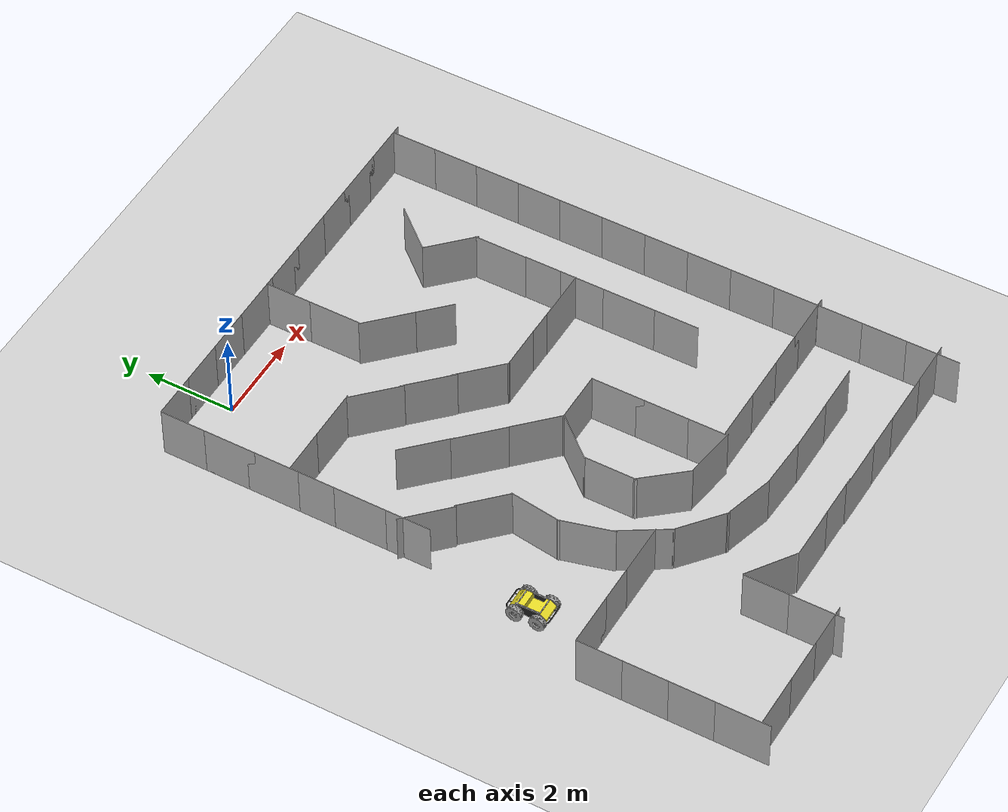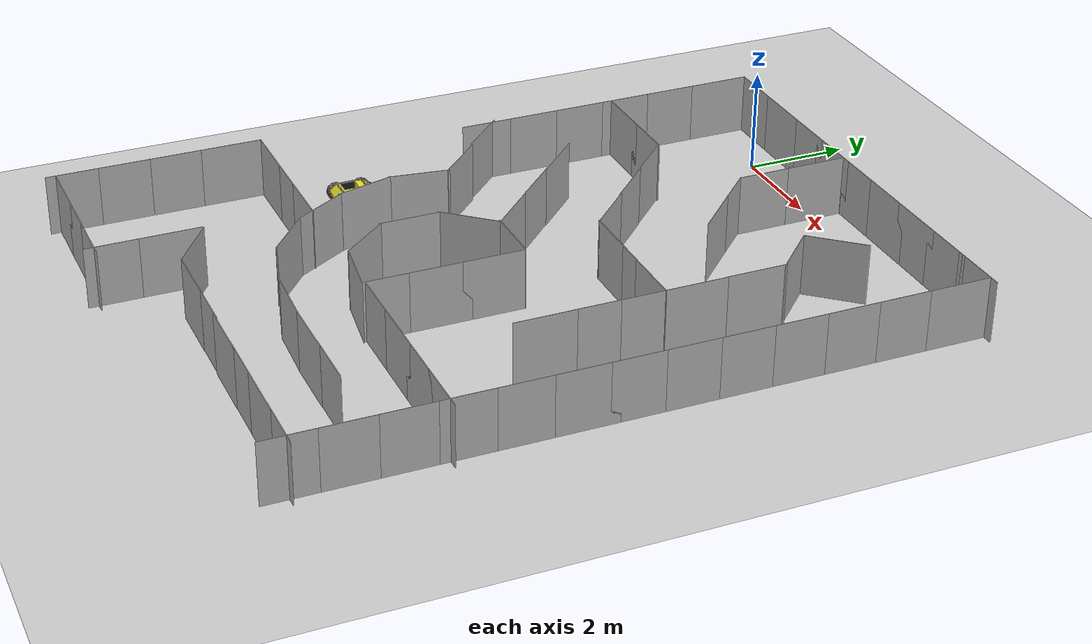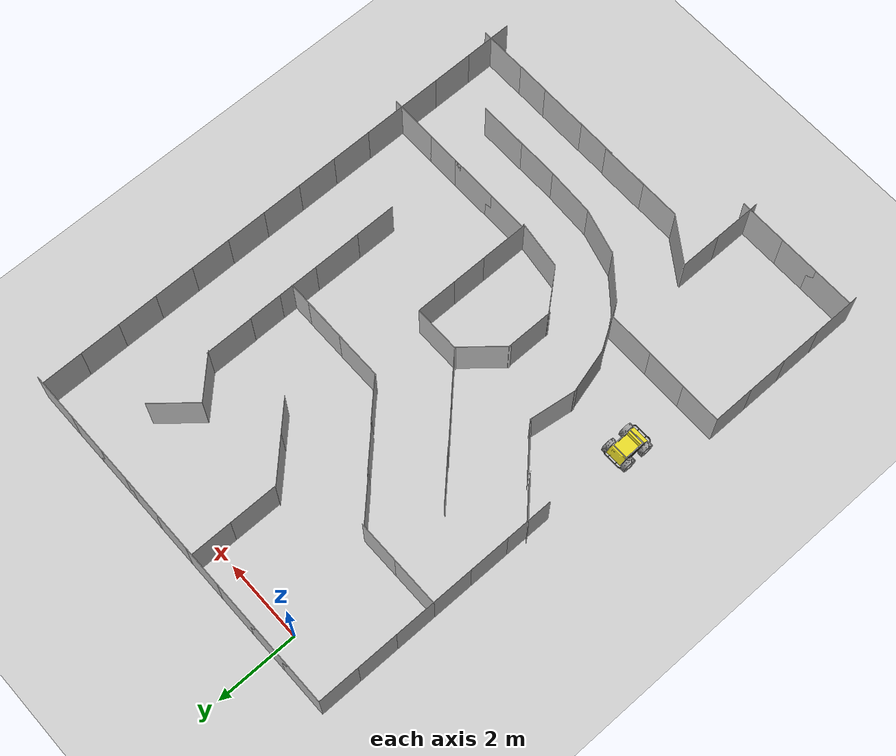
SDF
<sdf version="1.6">
 <world name="default">
  <light name="sun" type="directional">
   <pose>0 0 10 0 -0 0</pose>
   <diffuse>0.8 0.8 0.8 1</diffuse>
   <specular>0.2 0.2 0.2 1</specular>
   <attenuation>
    <range>1000</range>
    <constant>0.9</constant>
    <linear>0.01</linear>
    <quadratic>0.001</quadratic>
   </attenuation>
   <direction>-0.5 0.1 -0.9</direction>
  </light>
  <model name="ground_plane">
   <static>1</static>
   <link name="link">
    <collision name="collision">
     <geometry><plane><normal>0 0 1</normal><size>100 100</size></plane></geometry>
     <surface>
      <contact><collide_bitmask>65535</collide_bitmask></contact>
      <friction><ode><mu>100</mu><mu2>50</mu2></ode></friction>
     </surface>
    </collision>
    <visual name="visual">
     <cast_shadows>0</cast_shadows>
     <geometry><plane><normal>0 0 1</normal><size>100 100</size></plane></geometry>
     <material>
      <script><uri>file://media/materials/scripts/gazebo.material</uri><name>Gazebo/Grey</name></script>
     </material>
    </visual>
   </link>
  </model>
  <gravity>0 0 -9.8</gravity>
  <magnetic_field>6e-06 2.3e-05 -4.2e-05</magnetic_field>
  <atmosphere type="adiabatic"/>
  <physics name="default_physics" default="0" type="ode">
   <max_step_size>0.001</max_step_size>
   <real_time_factor>1</real_time_factor>
   <real_time_update_rate>1000</real_time_update_rate>
  </physics>
  <scene><ambient>0.4 0.4 0.4 1</ambient><background>0.7 0.7 0.7 1</background><shadows>1</shadows></scene>
  <audio><device>default</device></audio>
  <spherical_coordinates>
   <surface_model>EARTH_WGS84</surface_model>
   <latitude_deg>0</latitude_deg>
   <longitude_deg>0</longitude_deg>
   <elevation>0</elevation>
   <heading_deg>0</heading_deg>
  </spherical_coordinates>
  <model name="nist_maze_wall_120">
   <static>1</static>
   <link name="nist_maze_wall_120_link">
    <collision name="collision">
     <geometry>
      <mesh><uri>model://nist_maze_wall_120/meshes/nist_maze_wall_120.dae</uri><scale>1 1 1</scale></mesh>
     </geometry>
    </collision>
    <visual name="visual">
     <geometry>
      <mesh><uri>model://nist_maze_wall_120/meshes/nist_maze_wall_120.dae</uri><scale>1 1 1</scale></mesh>
     </geometry>
    </visual>
   </link>
   <pose>-1 0 0 0 -0 0</pose>
  </model>
  <model name="nist_maze_wall_120_clone">
   <static>1</static>
   <link name="nist_maze_wall_120_link">
    <collision name="collision">
     <geometry>
      <mesh><uri>model://nist_maze_wall_120/meshes/nist_maze_wall_120.dae</uri><scale>1 1 1</scale></mesh>
     </geometry>
    </collision>
    <visual name="visual">
     <geometry>
      <mesh><uri>model://nist_maze_wall_120/meshes/nist_maze_wall_120.dae</uri><scale>1 1 1</scale></mesh>
     </geometry>
    </visual>
   </link>
  </model>
  <model name="nist_maze_wall_120_clone_0">
   <static>1</static>
   <link name="nist_maze_wall_120_link">
    <collision name="collision">
     <geometry>
      <mesh><uri>model://nist_maze_wall_120/meshes/nist_maze_wall_120.dae</uri><scale>1 1 1</scale></mesh>
     </geometry>
    </collision>
    <visual name="visual">
     <geometry>
      <mesh><uri>model://nist_maze_wall_120/meshes/nist_maze_wall_120.dae</uri><scale>1 1 1</scale></mesh>
     </geometry>
    </visual>
   </link>
   <pose>1 0 0 0 -0 0</pose>
  </model>
  <model name="nist_maze_wall_120_clone_0_clone_2">
   <static>1</static>
   <link name="nist_maze_wall_120_link">
    <collision name="collision">
     <geometry>
      <mesh><uri>model://nist_maze_wall_120/meshes/nist_maze_wall_120.dae</uri><scale>1 1 1</scale></mesh>
     </geometry>
    </collision>
    <visual name="visual">
     <geometry>
      <mesh><uri>model://nist_maze_wall_120/meshes/nist_maze_wall_120.dae</uri><scale>1 1 1</scale></mesh>
     </geometry>
    </visual>
   </link>
   <pose>4 0 0 0 -0 0</pose>
  </model>
  <model name="nist_maze_wall_120_clone_0_clone_7">
   <static>1</static>
   <link name="nist_maze_wall_120_link">
    <collision name="collision">
     <geometry>
      <mesh><uri>model://nist_maze_wall_120/meshes/nist_maze_wall_120.dae</uri><scale>1 1 1</scale></mesh>
     </geometry>
    </collision>
    <visual name="visual">
     <geometry>
      <mesh><uri>model://nist_maze_wall_120/meshes/nist_maze_wall_120.dae</uri><scale>1 1 1</scale></mesh>
     </geometry>
    </visual>
   </link>
   <pose>5 0 0 0 -0 0</pose>
  </model>
  <model name="nist_maze_wall_120_clone_0_clone_8">
   <static>1</static>
   <link name="nist_maze_wall_120_link">
    <collision name="collision">
     <geometry>
      <mesh><uri>model://nist_maze_wall_120/meshes/nist_maze_wall_120.dae</uri><scale>1 1 1</scale></mesh>
     </geometry>
    </collision>
    <visual name="visual">
     <geometry>
      <mesh><uri>model://nist_maze_wall_120/meshes/nist_maze_wall_120.dae</uri><scale>1 1 1</scale></mesh>
     </geometry>
    </visual>
   </link>
   <pose>6 0 0 0 -0 0</pose>
  </model>
  <model name="nist_maze_wall_120_clone_0_clone_9">
   <static>1</static>
   <link name="nist_maze_wall_120_link">
    <collision name="collision">
     <geometry>
      <mesh><uri>model://nist_maze_wall_120/meshes/nist_maze_wall_120.dae</uri><scale>1 1 1</scale></mesh>
     </geometry>
    </collision>
    <visual name="visual">
     <geometry>
      <mesh><uri>model://nist_maze_wall_120/meshes/nist_maze_wall_120.dae</uri><scale>1 1 1</scale></mesh>
     </geometry>
    </visual>
   </link>
   <pose>2.36851 -2.42794 -0 0 0 -0.785398</pose>
  </model>
  <model name="nist_maze_wall_120_clone_0_clone_0_clone">
   <static>1</static>
   <link name="nist_maze_wall_120_link">
    <collision name="collision">
     <geometry>
      <mesh><uri>model://nist_maze_wall_120/meshes/nist_maze_wall_120.dae</uri><scale>1 1 1</scale></mesh>
     </geometry>
    </collision>
    <visual name="visual">
     <geometry>
      <mesh><uri>model://nist_maze_wall_120/meshes/nist_maze_wall_120.dae</uri><scale>1 1 1</scale></mesh>
     </geometry>
    </visual>
   </link>
   <pose>2 0 0 0 -0 0</pose>
  </model>
  <model name="nist_maze_wall_120_clone_0_clone_8_clone">
   <static>1</static>
   <link name="nist_maze_wall_120_link">
    <collision name="collision">
     <geometry>
      <mesh><uri>model://nist_maze_wall_120/meshes/nist_maze_wall_120.dae</uri><scale>1 1 1</scale></mesh>
     </geometry>
    </collision>
    <visual name="visual">
     <geometry>
      <mesh><uri>model://nist_maze_wall_120/meshes/nist_maze_wall_120.dae</uri><scale>1 1 1</scale></mesh>
     </geometry>
    </visual>
   </link>
   <pose>3 -1 0 0 -0 1.5708</pose>
  </model>
  <model name="nist_maze_wall_120_clone_0_clone_8_clone_clone">
   <static>1</static>
   <link name="nist_maze_wall_120_link">
    <collision name="collision">
     <geometry>
      <mesh><uri>model://nist_maze_wall_120/meshes/nist_maze_wall_120.dae</uri><scale>1 1 1</scale></mesh>
     </geometry>
    </collision>
    <visual name="visual">
     <geometry>
      <mesh><uri>model://nist_maze_wall_120/meshes/nist_maze_wall_120.dae</uri><scale>1 1 1</scale></mesh>
     </geometry>
    </visual>
   </link>
   <pose>3 0 0 0 -0 1.5708</pose>
  </model>
  <model name="nist_maze_wall_120_clone_0_clone_8_clone_clone_0">
   <static>1</static>
   <link name="nist_maze_wall_120_link">
    <collision name="collision">
     <geometry>
      <mesh><uri>model://nist_maze_wall_120/meshes/nist_maze_wall_120.dae</uri><scale>1 1 1</scale></mesh>
     </geometry>
    </collision>
    <visual name="visual">
     <geometry>
      <mesh><uri>model://nist_maze_wall_120/meshes/nist_maze_wall_120.dae</uri><scale>1 1 1</scale></mesh>
     </geometry>
    </visual>
   </link>
   <pose>6.24673 -4.15515 0 0 -0 1.5708</pose>
  </model>
  <model name="nist_maze_wall_120_clone_0_clone_8_clone_clone_1">
   <static>1</static>
   <link name="nist_maze_wall_120_link">
    <collision name="collision">
     <geometry>
      <mesh><uri>model://nist_maze_wall_120/meshes/nist_maze_wall_120.dae</uri><scale>1 1 1</scale></mesh>
     </geometry>
    </collision>
    <visual name="visual">
     <geometry>
      <mesh><uri>model://nist_maze_wall_120/meshes/nist_maze_wall_120.dae</uri><scale>1 1 1</scale></mesh>
     </geometry>
    </visual>
   </link>
   <pose>6.2388 -3 0 0 -0 1.5708</pose>
  </model>
  <model name="nist_maze_wall_120_clone_0_clone_8_clone_clone_2">
   <static>1</static>
   <link name="nist_maze_wall_120_link">
    <collision name="collision">
     <geometry>
      <mesh><uri>model://nist_maze_wall_120/meshes/nist_maze_wall_120.dae</uri><scale>1 1 1</scale></mesh>
     </geometry>
    </collision>
    <visual name="visual">
     <geometry>
      <mesh><uri>model://nist_maze_wall_120/meshes/nist_maze_wall_120.dae</uri><scale>1 1 1</scale></mesh>
     </geometry>
    </visual>
   </link>
   <pose>8 -2 0 0 -0 1.5708</pose>
  </model>
  <model name="nist_maze_wall_120_clone_0_clone_8_clone_clone_3">
   <static>1</static>
   <link name="nist_maze_wall_120_link">
    <collision name="collision">
     <geometry>
      <mesh><uri>model://nist_maze_wall_120/meshes/nist_maze_wall_120.dae</uri><scale>1 1 1</scale></mesh>
     </geometry>
    </collision>
    <visual name="visual">
     <geometry>
      <mesh><uri>model://nist_maze_wall_120/meshes/nist_maze_wall_120.dae</uri><scale>1 1 1</scale></mesh>
     </geometry>
    </visual>
   </link>
   <pose>8 0 0 0 -0 1.5708</pose>
  </model>
  <model name="nist_maze_wall_120_clone_0_clone_8_clone_clone_4">
   <static>1</static>
   <link name="nist_maze_wall_120_link">
    <collision name="collision">
     <geometry>
      <mesh><uri>model://nist_maze_wall_120/meshes/nist_maze_wall_120.dae</uri><scale>1 1 1</scale></mesh>
     </geometry>
    </collision>
    <visual name="visual">
     <geometry>
      <mesh><uri>model://nist_maze_wall_120/meshes/nist_maze_wall_120.dae</uri><scale>1 1 1</scale></mesh>
     </geometry>
    </visual>
   </link>
   <pose>8 -1 0 0 -0 1.5708</pose>
  </model>
  <model name="nist_maze_wall_120_clone_0_clone_8_clone_clone_5">
   <static>1</static>
   <link name="nist_maze_wall_120_link">
    <collision name="collision">
     <geometry>
      <mesh><uri>model://nist_maze_wall_120/meshes/nist_maze_wall_120.dae</uri><scale>1 1 1</scale></mesh>
     </geometry>
    </collision>
    <visual name="visual">
     <geometry>
      <mesh><uri>model://nist_maze_wall_120/meshes/nist_maze_wall_120.dae</uri><scale>1 1 1</scale></mesh>
     </geometry>
    </visual>
   </link>
   <pose>8 -4 0 0 -0 1.5708</pose>
  </model>
  <model name="nist_maze_wall_120_clone_0_clone_8_clone_clone_6">
   <static>1</static>
   <link name="nist_maze_wall_120_link">
    <collision name="collision">
     <geometry>
      <mesh><uri>model://nist_maze_wall_120/meshes/nist_maze_wall_120.dae</uri><scale>1 1 1</scale></mesh>
     </geometry>
    </collision>
    <visual name="visual">
     <geometry>
      <mesh><uri>model://nist_maze_wall_120/meshes/nist_maze_wall_120.dae</uri><scale>1 1 1</scale></mesh>
     </geometry>
    </visual>
   </link>
   <pose>-1 0 0 0 -0 1.5708</pose>
  </model>
  <model name="nist_maze_wall_120_clone_0_clone_8_clone_clone_7">
   <static>1</static>
   <link name="nist_maze_wall_120_link">
    <collision name="collision">
     <geometry>
      <mesh><uri>model://nist_maze_wall_120/meshes/nist_maze_wall_120.dae</uri><scale>1 1 1</scale></mesh>
     </geometry>
    </collision>
    <visual name="visual">
     <geometry>
      <mesh><uri>model://nist_maze_wall_120/meshes/nist_maze_wall_120.dae</uri><scale>1 1 1</scale></mesh>
     </geometry>
    </visual>
   </link>
   <pose>-1 -1 0 0 -0 1.5708</pose>
  </model>
  <model name="nist_maze_wall_120_clone_0_clone_8_clone_clone_11">
   <static>1</static>
   <link name="nist_maze_wall_120_link">
    <collision name="collision">
     <geometry>
      <mesh><uri>model://nist_maze_wall_120/meshes/nist_maze_wall_120.dae</uri><scale>1 1 1</scale></mesh>
     </geometry>
    </collision>
    <visual name="visual">
     <geometry>
      <mesh><uri>model://nist_maze_wall_120/meshes/nist_maze_wall_120.dae</uri><scale>1 1 1</scale></mesh>
     </geometry>
    </visual>
   </link>
   <pose>-1 -2 0 0 -0 1.5708</pose>
  </model>
  <model name="nist_maze_wall_120_clone_1">
   <static>1</static>
   <link name="nist_maze_wall_120_link">
    <collision name="collision">
     <geometry>
      <mesh><uri>model://nist_maze_wall_120/meshes/nist_maze_wall_120.dae</uri><scale>1 1 1</scale></mesh>
     </geometry>
    </collision>
    <visual name="visual">
     <geometry>
      <mesh><uri>model://nist_maze_wall_120/meshes/nist_maze_wall_120.dae</uri><scale>1 1 1</scale></mesh>
     </geometry>
    </visual>
   </link>
   <pose>-1 -3 0 0 -0 0</pose>
  </model>
  <model name="nist_maze_wall_120_clone_2">
   <static>1</static>
   <link name="nist_maze_wall_120_link">
    <collision name="collision">
     <geometry>
      <mesh><uri>model://nist_maze_wall_120/meshes/nist_maze_wall_120.dae</uri><scale>1 1 1</scale></mesh>
     </geometry>
    </collision>
    <visual name="visual">
     <geometry>
      <mesh><uri>model://nist_maze_wall_120/meshes/nist_maze_wall_120.dae</uri><scale>1 1 1</scale></mesh>
     </geometry>
    </visual>
   </link>
   <pose>0 -3 0 0 -0 0</pose>
  </model>
  <model name="nist_maze_wall_120_clone_3">
   <static>1</static>
   <link name="nist_maze_wall_120_link">
    <collision name="collision">
     <geometry>
      <mesh><uri>model://nist_maze_wall_120/meshes/nist_maze_wall_120.dae</uri><scale>1 1 1</scale></mesh>
     </geometry>
    </collision>
    <visual name="visual">
     <geometry>
      <mesh><uri>model://nist_maze_wall_120/meshes/nist_maze_wall_120.dae</uri><scale>1 1 1</scale></mesh>
     </geometry>
    </visual>
   </link>
   <pose>3.49655 -5.35182 0 0 -0 0</pose>
  </model>
  <model name="nist_maze_wall_120_clone_4">
   <static>1</static>
   <link name="nist_maze_wall_120_link">
    <collision name="collision">
     <geometry>
      <mesh><uri>model://nist_maze_wall_120/meshes/nist_maze_wall_120.dae</uri><scale>1 1 1</scale></mesh>
     </geometry>
    </collision>
    <visual name="visual">
     <geometry>
      <mesh><uri>model://nist_maze_wall_120/meshes/nist_maze_wall_120.dae</uri><scale>1 1 1</scale></mesh>
     </geometry>
    </visual>
   </link>
   <pose>5.06837 -5.36174 0 0 -0 0</pose>
  </model>
  <model name="nist_maze_wall_120_clone_5">
   <static>1</static>
   <link name="nist_maze_wall_120_link">
    <collision name="collision">
     <geometry>
      <mesh><uri>model://nist_maze_wall_120/meshes/nist_maze_wall_120.dae</uri><scale>1 1 1</scale></mesh>
     </geometry>
    </collision>
    <visual name="visual">
     <geometry>
      <mesh><uri>model://nist_maze_wall_120/meshes/nist_maze_wall_120.dae</uri><scale>1 1 1</scale></mesh>
     </geometry>
    </visual>
   </link>
   <pose>5.67552 -1.56373 0 0 -0 0.859737</pose>
  </model>
  <model name="nist_maze_wall_120_clone_6">
   <static>1</static>
   <link name="nist_maze_wall_120_link">
    <collision name="collision">
     <geometry>
      <mesh><uri>model://nist_maze_wall_120/meshes/nist_maze_wall_120.dae</uri><scale>1 1 1</scale></mesh>
     </geometry>
    </collision>
    <visual name="visual">
     <geometry>
      <mesh><uri>model://nist_maze_wall_120/meshes/nist_maze_wall_120.dae</uri><scale>1 1 1</scale></mesh>
     </geometry>
    </visual>
   </link>
   <pose>3 0 0 0 -0 0</pose>
  </model>
  <model name="nist_maze_wall_120_clone_7">
   <static>1</static>
   <link name="nist_maze_wall_120_link">
    <collision name="collision">
     <geometry>
      <mesh><uri>model://nist_maze_wall_120/meshes/nist_maze_wall_120.dae</uri><scale>1 1 1</scale></mesh>
     </geometry>
    </collision>
    <visual name="visual">
     <geometry>
      <mesh><uri>model://nist_maze_wall_120/meshes/nist_maze_wall_120.dae</uri><scale>1 1 1</scale></mesh>
     </geometry>
    </visual>
   </link>
   <pose>4.52175 -5.3564 0 0 -0 0</pose>
  </model>
  <model name="nist_maze_wall_120_clone_0_clone_9_clone">
   <static>1</static>
   <link name="nist_maze_wall_120_link">
    <collision name="collision">
     <geometry>
      <mesh><uri>model://nist_maze_wall_120/meshes/nist_maze_wall_120.dae</uri><scale>1 1 1</scale></mesh>
     </geometry>
    </collision>
    <visual name="visual">
     <geometry>
      <mesh><uri>model://nist_maze_wall_120/meshes/nist_maze_wall_120.dae</uri><scale>1 1 1</scale></mesh>
     </geometry>
    </visual>
   </link>
   <pose>2.95445 -3.01156 0 0 0 -0.785398</pose>
  </model>
  <model name="nist_maze_wall_120_clone_0_clone_9_clone_0">
   <static>1</static>
   <link name="nist_maze_wall_120_link">
    <collision name="collision">
     <geometry>
      <mesh><uri>model://nist_maze_wall_120/meshes/nist_maze_wall_120.dae</uri><scale>1 1 1</scale></mesh>
     </geometry>
    </collision>
    <visual name="visual">
     <geometry>
      <mesh><uri>model://nist_maze_wall_120/meshes/nist_maze_wall_120.dae</uri><scale>1 1 1</scale></mesh>
     </geometry>
    </visual>
   </link>
   <pose>0.538359 -3.24676 0 0 0 -0.785398</pose>
  </model>
  <model name="nist_maze_wall_120_clone_0_clone_9_clone_1">
   <static>1</static>
   <link name="nist_maze_wall_120_link">
    <collision name="collision">
     <geometry>
      <mesh><uri>model://nist_maze_wall_120/meshes/nist_maze_wall_120.dae</uri><scale>1 1 1</scale></mesh>
     </geometry>
    </collision>
    <visual name="visual">
     <geometry>
      <mesh><uri>model://nist_maze_wall_120/meshes/nist_maze_wall_120.dae</uri><scale>1 1 1</scale></mesh>
     </geometry>
    </visual>
   </link>
   <pose>1.32503 -4.012 0 0 0 -0.785398</pose>
  </model>
  <model name="nist_maze_wall_120_clone_0_clone_9_clone_2">
   <static>1</static>
   <link name="nist_maze_wall_120_link">
    <collision name="collision">
     <geometry>
      <mesh><uri>model://nist_maze_wall_120/meshes/nist_maze_wall_120.dae</uri><scale>1 1 1</scale></mesh>
     </geometry>
    </collision>
    <visual name="visual">
     <geometry>
      <mesh><uri>model://nist_maze_wall_120/meshes/nist_maze_wall_120.dae</uri><scale>1 1 1</scale></mesh>
     </geometry>
    </visual>
   </link>
   <pose>2.09964 -4.76804 0 0 0 -0.785398</pose>
  </model>
  <model name="nist_maze_wall_120_clone_0_clone_8_clone_0">
   <static>1</static>
   <link name="nist_maze_wall_120_link">
    <collision name="collision">
     <geometry>
      <mesh><uri>model://nist_maze_wall_120/meshes/nist_maze_wall_120.dae</uri><scale>1 1 1</scale></mesh>
     </geometry>
    </collision>
    <visual name="visual">
     <geometry>
      <mesh><uri>model://nist_maze_wall_120/meshes/nist_maze_wall_120.dae</uri><scale>1 1 1</scale></mesh>
     </geometry>
    </visual>
   </link>
   <pose>7 0 0 0 -0 0</pose>
  </model>
  <model name="nist_maze_wall_120_clone_0_clone_8_clone_clone_2_clone">
   <static>1</static>
   <link name="nist_maze_wall_120_link">
    <collision name="collision">
     <geometry>
      <mesh><uri>model://nist_maze_wall_120/meshes/nist_maze_wall_120.dae</uri><scale>1 1 1</scale></mesh>
     </geometry>
    </collision>
    <visual name="visual">
     <geometry>
      <mesh><uri>model://nist_maze_wall_120/meshes/nist_maze_wall_120.dae</uri><scale>1 1 1</scale></mesh>
     </geometry>
    </visual>
   </link>
   <pose>8 -3 0 0 -0 1.5708</pose>
  </model>
  <model name="nist_maze_wall_120_clone_0_clone_9_clone_clone">
   <static>1</static>
   <link name="nist_maze_wall_120_link">
    <collision name="collision">
     <geometry>
      <mesh><uri>model://nist_maze_wall_120/meshes/nist_maze_wall_120.dae</uri><scale>1 1 1</scale></mesh>
     </geometry>
    </collision>
    <visual name="visual">
     <geometry>
      <mesh><uri>model://nist_maze_wall_120/meshes/nist_maze_wall_120.dae</uri><scale>1 1 1</scale></mesh>
     </geometry>
    </visual>
   </link>
   <pose>4.82694 -2.46879 0 0 0 -0.785398</pose>
  </model>
  <model name="nist_maze_wall_120_clone_0_clone_8_clone_clone_5_clone">
   <static>1</static>
   <link name="nist_maze_wall_120_link">
    <collision name="collision">
     <geometry>
      <mesh><uri>model://nist_maze_wall_120/meshes/nist_maze_wall_120.dae</uri><scale>1 1 1</scale></mesh>
     </geometry>
    </collision>
    <visual name="visual">
     <geometry>
      <mesh><uri>model://nist_maze_wall_120/meshes/nist_maze_wall_120.dae</uri><scale>1 1 1</scale></mesh>
     </geometry>
    </visual>
   </link>
   <pose>8 -5 0 0 -0 1.5708</pose>
  </model>
  <model name="nist_maze_wall_120_clone_0_clone_8_clone_clone_5_clone_0">
   <static>1</static>
   <link name="nist_maze_wall_120_link">
    <collision name="collision">
     <geometry>
      <mesh><uri>model://nist_maze_wall_120/meshes/nist_maze_wall_120.dae</uri><scale>1 1 1</scale></mesh>
     </geometry>
    </collision>
    <visual name="visual">
     <geometry>
      <mesh><uri>model://nist_maze_wall_120/meshes/nist_maze_wall_120.dae</uri><scale>1 1 1</scale></mesh>
     </geometry>
    </visual>
   </link>
   <pose>8 -6 0 0 -0 1.5708</pose>
  </model>
  <model name="nist_maze_wall_120_clone_0_clone_8_clone_clone_5_clone_1">
   <static>1</static>
   <link name="nist_maze_wall_120_link">
    <collision name="collision">
     <geometry>
      <mesh><uri>model://nist_maze_wall_120/meshes/nist_maze_wall_120.dae</uri><scale>1 1 1</scale></mesh>
     </geometry>
    </collision>
    <visual name="visual">
     <geometry>
      <mesh><uri>model://nist_maze_wall_120/meshes/nist_maze_wall_120.dae</uri><scale>1 1 1</scale></mesh>
     </geometry>
    </visual>
   </link>
   <pose>8 -7 0 0 -0 1.5708</pose>
  </model>
  <model name="nist_maze_wall_120_clone_0_clone_8_clone_clone_5_clone_2">
   <static>1</static>
   <link name="nist_maze_wall_120_link">
    <collision name="collision">
     <geometry>
      <mesh><uri>model://nist_maze_wall_120/meshes/nist_maze_wall_120.dae</uri><scale>1 1 1</scale></mesh>
     </geometry>
    </collision>
    <visual name="visual">
     <geometry>
      <mesh><uri>model://nist_maze_wall_120/meshes/nist_maze_wall_120.dae</uri><scale>1 1 1</scale></mesh>
     </geometry>
    </visual>
   </link>
   <pose>8 -8 0 0 -0 1.5708</pose>
  </model>
  <model name="nist_maze_wall_120_clone_0_clone_8_clone_clone_5_clone_3">
   <static>1</static>
   <link name="nist_maze_wall_120_link">
    <collision name="collision">
     <geometry>
      <mesh><uri>model://nist_maze_wall_120/meshes/nist_maze_wall_120.dae</uri><scale>1 1 1</scale></mesh>
     </geometry>
    </collision>
    <visual name="visual">
     <geometry>
      <mesh><uri>model://nist_maze_wall_120/meshes/nist_maze_wall_120.dae</uri><scale>1 1 1</scale></mesh>
     </geometry>
    </visual>
   </link>
   <pose>8 -9 0 0 -0 1.5708</pose>
  </model>
  <model name="nist_maze_wall_120_clone_0_clone_8_clone_clone_5_clone_4">
   <static>1</static>
   <link name="nist_maze_wall_120_link">
    <collision name="collision">
     <geometry>
      <mesh><uri>model://nist_maze_wall_120/meshes/nist_maze_wall_120.dae</uri><scale>1 1 1</scale></mesh>
     </geometry>
    </collision>
    <visual name="visual">
     <geometry>
      <mesh><uri>model://nist_maze_wall_120/meshes/nist_maze_wall_120.dae</uri><scale>1 1 1</scale></mesh>
     </geometry>
    </visual>
   </link>
   <pose>6.245 -5 0 0 -0 1.5708</pose>
  </model>
  <model name="nist_maze_wall_120_clone_0_clone_8_clone_clone_5_clone_5">
   <static>1</static>
   <link name="nist_maze_wall_120_link">
    <collision name="collision">
     <geometry>
      <mesh><uri>model://nist_maze_wall_120/meshes/nist_maze_wall_120.dae</uri><scale>1 1 1</scale></mesh>
     </geometry>
    </collision>
    <visual name="visual">
     <geometry>
      <mesh><uri>model://nist_maze_wall_120/meshes/nist_maze_wall_120.dae</uri><scale>1 1 1</scale></mesh>
     </geometry>
    </visual>
   </link>
   <pose>6.2446 -6 0 0 -0 1.5708</pose>
  </model>
  <model name="nist_maze_wall_120_clone_0_clone_8_clone_clone_5_clone_6">
   <static>1</static>
   <link name="nist_maze_wall_120_link">
    <collision name="collision">
     <geometry>
      <mesh><uri>model://nist_maze_wall_120/meshes/nist_maze_wall_120.dae</uri><scale>1 1 1</scale></mesh>
     </geometry>
    </collision>
    <visual name="visual">
     <geometry>
      <mesh><uri>model://nist_maze_wall_120/meshes/nist_maze_wall_120.dae</uri><scale>1 1 1</scale></mesh>
     </geometry>
    </visual>
   </link>
   <pose>6.24737 -7 0 0 -0 1.5708</pose>
  </model>
  <model name="nist_maze_wall_120_clone_7_clone">
   <static>1</static>
   <link name="nist_maze_wall_120_link">
    <collision name="collision">
     <geometry>
      <mesh><uri>model://nist_maze_wall_120/meshes/nist_maze_wall_120.dae</uri><scale>1 1 1</scale></mesh>
     </geometry>
    </collision>
    <visual name="visual">
     <geometry>
      <mesh><uri>model://nist_maze_wall_120/meshes/nist_maze_wall_120.dae</uri><scale>1 1 1</scale></mesh>
     </geometry>
    </visual>
   </link>
   <pose>7 -10 0 0 -0 0</pose>
  </model>
  <model name="nist_maze_wall_120_clone_7_clone_0">
   <static>1</static>
   <link name="nist_maze_wall_120_link">
    <collision name="collision">
     <geometry>
      <mesh><uri>model://nist_maze_wall_120/meshes/nist_maze_wall_120.dae</uri><scale>1 1 1</scale></mesh>
     </geometry>
    </collision>
    <visual name="visual">
     <geometry>
      <mesh><uri>model://nist_maze_wall_120/meshes/nist_maze_wall_120.dae</uri><scale>1 1 1</scale></mesh>
     </geometry>
    </visual>
   </link>
   <pose>6 -10 0 0 -0 0</pose>
  </model>
  <model name="nist_maze_wall_120_clone_7_clone_1">
   <static>1</static>
   <link name="nist_maze_wall_120_link">
    <collision name="collision">
     <geometry>
      <mesh><uri>model://nist_maze_wall_120/meshes/nist_maze_wall_120.dae</uri><scale>1 1 1</scale></mesh>
     </geometry>
    </collision>
    <visual name="visual">
     <geometry>
      <mesh><uri>model://nist_maze_wall_120/meshes/nist_maze_wall_120.dae</uri><scale>1 1 1</scale></mesh>
     </geometry>
    </visual>
   </link>
   <pose>5 -10 0 0 -0 0</pose>
  </model>
  <model name="nist_maze_wall_120_clone_7_clone_2">
   <static>1</static>
   <link name="nist_maze_wall_120_link">
    <collision name="collision">
     <geometry>
      <mesh><uri>model://nist_maze_wall_120/meshes/nist_maze_wall_120.dae</uri><scale>1 1 1</scale></mesh>
     </geometry>
    </collision>
    <visual name="visual">
     <geometry>
      <mesh><uri>model://nist_maze_wall_120/meshes/nist_maze_wall_120.dae</uri><scale>1 1 1</scale></mesh>
     </geometry>
    </visual>
   </link>
   <pose>4 -10 0 0 -0 0</pose>
  </model>
  <model name="nist_maze_wall_120_clone_0_clone_8_clone_clone_5_clone_6_clone">
   <static>1</static>
   <link name="nist_maze_wall_120_link">
    <collision name="collision">
     <geometry>
      <mesh><uri>model://nist_maze_wall_120/meshes/nist_maze_wall_120.dae</uri><scale>1 1 1</scale></mesh>
     </geometry>
    </collision>
    <visual name="visual">
     <geometry>
      <mesh><uri>model://nist_maze_wall_120/meshes/nist_maze_wall_120.dae</uri><scale>1 1 1</scale></mesh>
     </geometry>
    </visual>
   </link>
   <pose>4 -8.85445 0 0 -0 1.5708</pose>
  </model>
  <model name="nist_maze_wall_120_clone_0_clone_8_clone_clone_5_clone_6_clone_0">
   <static>1</static>
   <link name="nist_maze_wall_120_link">
    <collision name="collision">
     <geometry>
      <mesh><uri>model://nist_maze_wall_120/meshes/nist_maze_wall_120.dae</uri><scale>1 1 1</scale></mesh>
     </geometry>
    </collision>
    <visual name="visual">
     <geometry>
      <mesh><uri>model://nist_maze_wall_120/meshes/nist_maze_wall_120.dae</uri><scale>1 1 1</scale></mesh>
     </geometry>
    </visual>
   </link>
   <pose>4 -8 0 0 -0 1.5708</pose>
  </model>
  <model name="nist_maze_wall_120_clone_0_clone_8_clone_clone_5_clone_6_clone_1">
   <static>1</static>
   <link name="nist_maze_wall_120_link">
    <collision name="collision">
     <geometry>
      <mesh><uri>model://nist_maze_wall_120/meshes/nist_maze_wall_120.dae</uri><scale>1 1 1</scale></mesh>
     </geometry>
    </collision>
    <visual name="visual">
     <geometry>
      <mesh><uri>model://nist_maze_wall_120/meshes/nist_maze_wall_120.dae</uri><scale>1 1 1</scale></mesh>
     </geometry>
    </visual>
   </link>
   <pose>4 -7 0 0 -0 1.5708</pose>
  </model>
  <model name="nist_maze_wall_120_clone_0_clone_8_clone_clone_5_clone_6_clone_2">
   <static>1</static>
   <link name="nist_maze_wall_120_link">
    <collision name="collision">
     <geometry>
      <mesh><uri>model://nist_maze_wall_120/meshes/nist_maze_wall_120.dae</uri><scale>1 1 1</scale></mesh>
     </geometry>
    </collision>
    <visual name="visual">
     <geometry>
      <mesh><uri>model://nist_maze_wall_120/meshes/nist_maze_wall_120.dae</uri><scale>1 1 1</scale></mesh>
     </geometry>
    </visual>
   </link>
   <pose>-1 -3 0 0 -0 1.5708</pose>
  </model>
  <model name="nist_maze_wall_120_clone_0_clone_8_clone_clone_5_clone_6_clone_3">
   <static>1</static>
   <link name="nist_maze_wall_120_link">
    <collision name="collision">
     <geometry>
      <mesh><uri>model://nist_maze_wall_120/meshes/nist_maze_wall_120.dae</uri><scale>1 1 1</scale></mesh>
     </geometry>
    </collision>
    <visual name="visual">
     <geometry>
      <mesh><uri>model://nist_maze_wall_120/meshes/nist_maze_wall_120.dae</uri><scale>1 1 1</scale></mesh>
     </geometry>
    </visual>
   </link>
   <pose>-1 -4 0 0 -0 1.5708</pose>
  </model>
  <model name="nist_maze_wall_120_clone_0_clone_8_clone_clone_5_clone_6_clone_4">
   <static>1</static>
   <link name="nist_maze_wall_120_link">
    <collision name="collision">
     <geometry>
      <mesh><uri>model://nist_maze_wall_120/meshes/nist_maze_wall_120.dae</uri><scale>1 1 1</scale></mesh>
     </geometry>
    </collision>
    <visual name="visual">
     <geometry>
      <mesh><uri>model://nist_maze_wall_120/meshes/nist_maze_wall_120.dae</uri><scale>1 1 1</scale></mesh>
     </geometry>
    </visual>
   </link>
   <pose>-1 -5 0 0 -0 1.5708</pose>
  </model>
  <model name="nist_maze_wall_120_clone_3_clone">
   <static>1</static>
   <link name="nist_maze_wall_120_link">
    <collision name="collision">
     <geometry>
      <mesh><uri>model://nist_maze_wall_120/meshes/nist_maze_wall_120.dae</uri><scale>1 1 1</scale></mesh>
     </geometry>
    </collision>
    <visual name="visual">
     <geometry>
      <mesh><uri>model://nist_maze_wall_120/meshes/nist_maze_wall_120.dae</uri><scale>1 1 1</scale></mesh>
     </geometry>
    </visual>
   </link>
   <pose>2.80885 -7 0 0 -0 0</pose>
  </model>
  <model name="nist_maze_wall_120_clone_0_clone_9_clone_2_clone">
   <static>1</static>
   <link name="nist_maze_wall_120_link">
    <collision name="collision">
     <geometry>
      <mesh><uri>model://nist_maze_wall_120/meshes/nist_maze_wall_120.dae</uri><scale>1 1 1</scale></mesh>
     </geometry>
    </collision>
    <visual name="visual">
     <geometry>
      <mesh><uri>model://nist_maze_wall_120/meshes/nist_maze_wall_120.dae</uri><scale>1 1 1</scale></mesh>
     </geometry>
    </visual>
   </link>
   <pose>1.42168 -6.40993 0 0 0 -0.785398</pose>
  </model>
  <model name="nist_maze_wall_120_clone_0_clone_9_clone_2_clone_0">
   <static>1</static>
   <link name="nist_maze_wall_120_link">
    <collision name="collision">
     <geometry>
      <mesh><uri>model://nist_maze_wall_120/meshes/nist_maze_wall_120.dae</uri><scale>1 1 1</scale></mesh>
     </geometry>
    </collision>
    <visual name="visual">
     <geometry>
      <mesh><uri>model://nist_maze_wall_120/meshes/nist_maze_wall_120.dae</uri><scale>1 1 1</scale></mesh>
     </geometry>
    </visual>
   </link>
   <pose>0.613898 -5.6077 0 0 0 -0.785398</pose>
  </model>
  <model name="nist_maze_wall_120_clone_0_clone_9_clone_2_clone_1">
   <static>1</static>
   <link name="nist_maze_wall_120_link">
    <collision name="collision">
     <geometry>
      <mesh><uri>model://nist_maze_wall_120/meshes/nist_maze_wall_120.dae</uri><scale>1 1 1</scale></mesh>
     </geometry>
    </collision>
    <visual name="visual">
     <geometry>
      <mesh><uri>model://nist_maze_wall_120/meshes/nist_maze_wall_120.dae</uri><scale>1 1 1</scale></mesh>
     </geometry>
    </visual>
   </link>
   <pose>-0.170834 -4.81042 0 0 0 -0.785398</pose>
  </model>
  <model name="nist_maze_wall_120_clone_5_clone">
   <static>1</static>
   <link name="nist_maze_wall_120_link">
    <collision name="collision">
     <geometry>
      <mesh><uri>model://nist_maze_wall_120/meshes/nist_maze_wall_120.dae</uri><scale>1 1 1</scale></mesh>
     </geometry>
    </collision>
    <visual name="visual">
     <geometry>
      <mesh><uri>model://nist_maze_wall_120/meshes/nist_maze_wall_120.dae</uri><scale>1 1 1</scale></mesh>
     </geometry>
    </visual>
   </link>
   <pose>2.32285 -7.25423 0 0 -0 0.859737</pose>
  </model>
  <model name="nist_maze_wall_120_clone_5_clone_0">
   <static>1</static>
   <link name="nist_maze_wall_120_link">
    <collision name="collision">
     <geometry>
      <mesh><uri>model://nist_maze_wall_120/meshes/nist_maze_wall_120.dae</uri><scale>1 1 1</scale></mesh>
     </geometry>
    </collision>
    <visual name="visual">
     <geometry>
      <mesh><uri>model://nist_maze_wall_120/meshes/nist_maze_wall_120.dae</uri><scale>1 1 1</scale></mesh>
     </geometry>
    </visual>
   </link>
   <pose>0.510403 -7.16893 0 0 -0 1.4342</pose>
  </model>
  <model name="nist_maze_wall_120_clone_0_clone_9_clone_2_clone_1_clone">
   <static>1</static>
   <link name="nist_maze_wall_120_link">
    <collision name="collision">
     <geometry>
      <mesh><uri>model://nist_maze_wall_120/meshes/nist_maze_wall_120.dae</uri><scale>1 1 1</scale></mesh>
     </geometry>
    </collision>
    <visual name="visual">
     <geometry>
      <mesh><uri>model://nist_maze_wall_120/meshes/nist_maze_wall_120.dae</uri><scale>1 1 1</scale></mesh>
     </geometry>
    </visual>
   </link>
   <pose>-1.69028 -5.7396 0 0 0 -0.785398</pose>
  </model>
  <model name="nist_maze_wall_120_clone_0_clone_9_clone_2_clone_1_clone_0">
   <static>1</static>
   <link name="nist_maze_wall_120_link">
    <collision name="collision">
     <geometry>
      <mesh><uri>model://nist_maze_wall_120/meshes/nist_maze_wall_120.dae</uri><scale>1 1 1</scale></mesh>
     </geometry>
    </collision>
    <visual name="visual">
     <geometry>
      <mesh><uri>model://nist_maze_wall_120/meshes/nist_maze_wall_120.dae</uri><scale>1 1 1</scale></mesh>
     </geometry>
    </visual>
   </link>
   <pose>-0.839871 -6.54271 0 0 0 -0.785398</pose>
  </model>
  <model name="nist_maze_wall_120_clone_0_clone_8_clone_clone_5_clone_6_clone_3_clone_0">
   <static>1</static>
   <link name="nist_maze_wall_120_link">
    <collision name="collision">
     <geometry>
      <mesh><uri>model://nist_maze_wall_120/meshes/nist_maze_wall_120.dae</uri><scale>1 1 1</scale></mesh>
     </geometry>
    </collision>
    <visual name="visual">
     <geometry>
      <mesh><uri>model://nist_maze_wall_120/meshes/nist_maze_wall_120.dae</uri><scale>1 1 1</scale></mesh>
     </geometry>
    </visual>
   </link>
   <pose>2.10658 -7.87085 0 0 -0 1.5708</pose>
  </model>
  <model name="nist_maze_wall_120_clone_0_clone_8_clone_clone_5_clone_6_clone_3_clone_1">
   <static>1</static>
   <link name="nist_maze_wall_120_link">
    <collision name="collision">
     <geometry>
      <mesh><uri>model://nist_maze_wall_120/meshes/nist_maze_wall_120.dae</uri><scale>1 1 1</scale></mesh>
     </geometry>
    </collision>
    <visual name="visual">
     <geometry>
      <mesh><uri>model://nist_maze_wall_120/meshes/nist_maze_wall_120.dae</uri><scale>1 1 1</scale></mesh>
     </geometry>
    </visual>
   </link>
   <pose>2.33228 -8.47007 0 0 -0 2.26876</pose>
  </model>
  <model name="nist_maze_wall_120_clone_0_clone_8_clone_clone_5_clone_6_clone_3_clone_2">
   <static>1</static>
   <link name="nist_maze_wall_120_link">
    <collision name="collision">
     <geometry>
      <mesh><uri>model://nist_maze_wall_120/meshes/nist_maze_wall_120.dae</uri><scale>1 1 1</scale></mesh>
     </geometry>
    </collision>
    <visual name="visual">
     <geometry>
      <mesh><uri>model://nist_maze_wall_120/meshes/nist_maze_wall_120.dae</uri><scale>1 1 1</scale></mesh>
     </geometry>
    </visual>
   </link>
   <pose>2.92579 -8.78641 0 0 -0 3.00495</pose>
  </model>
  <model name="nist_maze_wall_120_clone_0_clone_8_clone_clone_5_clone_6_clone_3_clone_3">
   <static>1</static>
   <link name="nist_maze_wall_120_link">
    <collision name="collision">
     <geometry>
      <mesh><uri>model://nist_maze_wall_120/meshes/nist_maze_wall_120.dae</uri><scale>1 1 1</scale></mesh>
     </geometry>
    </collision>
    <visual name="visual">
     <geometry>
      <mesh><uri>model://nist_maze_wall_120/meshes/nist_maze_wall_120.dae</uri><scale>1 1 1</scale></mesh>
     </geometry>
    </visual>
   </link>
   <pose>0.569683 -8.03484 0 0 -0 1.8295</pose>
  </model>
  <model name="nist_maze_wall_120_clone_0_clone_8_clone_clone_5_clone_6_clone_3_clone_4">
   <static>1</static>
   <link name="nist_maze_wall_120_link">
    <collision name="collision">
     <geometry>
      <mesh><uri>model://nist_maze_wall_120/meshes/nist_maze_wall_120.dae</uri><scale>1 1 1</scale></mesh>
     </geometry>
    </collision>
    <visual name="visual">
     <geometry>
      <mesh><uri>model://nist_maze_wall_120/meshes/nist_maze_wall_120.dae</uri><scale>1 1 1</scale></mesh>
     </geometry>
    </visual>
   </link>
   <pose>-2 -10 0 0 -0 1.5708</pose>
  </model>
  <model name="nist_maze_wall_120_clone_0_clone_8_clone_clone_5_clone_6_clone_3_clone_5">
   <static>1</static>
   <link name="nist_maze_wall_120_link">
    <collision name="collision">
     <geometry>
      <mesh><uri>model://nist_maze_wall_120/meshes/nist_maze_wall_120.dae</uri><scale>1 1 1</scale></mesh>
     </geometry>
    </collision>
    <visual name="visual">
     <geometry>
      <mesh><uri>model://nist_maze_wall_120/meshes/nist_maze_wall_120.dae</uri><scale>1 1 1</scale></mesh>
     </geometry>
    </visual>
   </link>
   <pose>1.57844 -9.60506 0 0 -0 2.4552</pose>
  </model>
  <model name="nist_maze_wall_120_clone_7_clone_2_clone">
   <static>1</static>
   <link name="nist_maze_wall_120_link">
    <collision name="collision">
     <geometry>
      <mesh><uri>model://nist_maze_wall_120/meshes/nist_maze_wall_120.dae</uri><scale>1 1 1</scale></mesh>
     </geometry>
    </collision>
    <visual name="visual">
     <geometry>
      <mesh><uri>model://nist_maze_wall_120/meshes/nist_maze_wall_120.dae</uri><scale>1 1 1</scale></mesh>
     </geometry>
    </visual>
   </link>
   <pose>4.48548 -11.3853 0 0 -0 0</pose>
  </model>
  <model name="nist_maze_wall_120_clone_0_clone_8_clone_clone_5_clone_6_clone_3_clone_2_clone">
   <static>1</static>
   <link name="nist_maze_wall_120_link">
    <collision name="collision">
     <geometry>
      <mesh><uri>model://nist_maze_wall_120/meshes/nist_maze_wall_120.dae</uri><scale>1 1 1</scale></mesh>
     </geometry>
    </collision>
    <visual name="visual">
     <geometry>
      <mesh><uri>model://nist_maze_wall_120/meshes/nist_maze_wall_120.dae</uri><scale>1 1 1</scale></mesh>
     </geometry>
    </visual>
   </link>
   <pose>2.34612 -9.99977 0 0 -0 2.87086</pose>
  </model>
  <model name="nist_maze_wall_120_clone_0_clone_8_clone_clone_5_clone_6_clone_3_clone_1_clone">
   <static>1</static>
   <link name="nist_maze_wall_120_link">
    <collision name="collision">
     <geometry>
      <mesh><uri>model://nist_maze_wall_120/meshes/nist_maze_wall_120.dae</uri><scale>1 1 1</scale></mesh>
     </geometry>
    </collision>
    <visual name="visual">
     <geometry>
      <mesh><uri>model://nist_maze_wall_120/meshes/nist_maze_wall_120.dae</uri><scale>1 1 1</scale></mesh>
     </geometry>
    </visual>
   </link>
   <pose>0.957633 -8.89644 0 0 -0 2.1196</pose>
  </model>
  <model name="nist_maze_wall_120_clone_0_clone_8_clone_clone_5_clone_6_clone_3_clone_5_clone">
   <static>1</static>
   <link name="nist_maze_wall_120_link">
    <collision name="collision">
     <geometry>
      <mesh><uri>model://nist_maze_wall_120/meshes/nist_maze_wall_120.dae</uri><scale>1 1 1</scale></mesh>
     </geometry>
    </collision>
    <visual name="visual">
     <geometry>
      <mesh><uri>model://nist_maze_wall_120/meshes/nist_maze_wall_120.dae</uri><scale>1 1 1</scale></mesh>
     </geometry>
    </visual>
   </link>
   <pose>3.36215 -10.1581 0 0 -0 3.09679</pose>
  </model>
  <model name="nist_maze_wall_120_clone_7_clone_0_clone">
   <static>1</static>
   <link name="nist_maze_wall_120_link">
    <collision name="collision">
     <geometry>
      <mesh><uri>model://nist_maze_wall_120/meshes/nist_maze_wall_120.dae</uri><scale>1 1 1</scale></mesh>
     </geometry>
    </collision>
    <visual name="visual">
     <geometry>
      <mesh><uri>model://nist_maze_wall_120/meshes/nist_maze_wall_120.dae</uri><scale>1 1 1</scale></mesh>
     </geometry>
    </visual>
   </link>
   <pose>0 -10 0 0 -0 0</pose>
  </model>
  <model name="nist_maze_wall_120_clone_7_clone_0_clone_clone">
   <static>1</static>
   <link name="nist_maze_wall_120_link">
    <collision name="collision">
     <geometry>
      <mesh><uri>model://nist_maze_wall_120/meshes/nist_maze_wall_120.dae</uri><scale>1 1 1</scale></mesh>
     </geometry>
    </collision>
    <visual name="visual">
     <geometry>
      <mesh><uri>model://nist_maze_wall_120/meshes/nist_maze_wall_120.dae</uri><scale>1 1 1</scale></mesh>
     </geometry>
    </visual>
   </link>
   <pose>-1 -10 0 0 -0 0</pose>
  </model>
  <model name="nist_maze_wall_120_clone_0_clone_8_clone_clone_5_clone_6_clone_3_clone_4_clone">
   <static>1</static>
   <link name="nist_maze_wall_120_link">
    <collision name="collision">
     <geometry>
      <mesh><uri>model://nist_maze_wall_120/meshes/nist_maze_wall_120.dae</uri><scale>1 1 1</scale></mesh>
     </geometry>
    </collision>
    <visual name="visual">
     <geometry>
      <mesh><uri>model://nist_maze_wall_120/meshes/nist_maze_wall_120.dae</uri><scale>1 1 1</scale></mesh>
     </geometry>
    </visual>
   </link>
   <pose>-2 -11 0 0 -0 1.5708</pose>
  </model>
  <model name="nist_maze_wall_120_clone_0_clone_8_clone_clone_5_clone_6_clone_3_clone_4_clone_0">
   <static>1</static>
   <link name="nist_maze_wall_120_link">
    <collision name="collision">
     <geometry>
      <mesh><uri>model://nist_maze_wall_120/meshes/nist_maze_wall_120.dae</uri><scale>1 1 1</scale></mesh>
     </geometry>
    </collision>
    <visual name="visual">
     <geometry>
      <mesh><uri>model://nist_maze_wall_120/meshes/nist_maze_wall_120.dae</uri><scale>1 1 1</scale></mesh>
     </geometry>
    </visual>
   </link>
   <pose>-2 -12 0 0 -0 1.5708</pose>
  </model>
  <model name="nist_maze_wall_120_clone_0_clone_8_clone_clone_5_clone_6_clone_3_clone_4_clone_1">
   <static>1</static>
   <link name="nist_maze_wall_120_link">
    <collision name="collision">
     <geometry>
      <mesh><uri>model://nist_maze_wall_120/meshes/nist_maze_wall_120.dae</uri><scale>1 1 1</scale></mesh>
     </geometry>
    </collision>
    <visual name="visual">
     <geometry>
      <mesh><uri>model://nist_maze_wall_120/meshes/nist_maze_wall_120.dae</uri><scale>1 1 1</scale></mesh>
     </geometry>
    </visual>
   </link>
   <pose>-2 -13 0 0 -0 1.5708</pose>
  </model>
  <model name="nist_maze_wall_120_clone_0_clone_8_clone_clone_5_clone_6_clone_3_clone_4_clone_2">
   <static>1</static>
   <link name="nist_maze_wall_120_link">
    <collision name="collision">
     <geometry>
      <mesh><uri>model://nist_maze_wall_120/meshes/nist_maze_wall_120.dae</uri><scale>1 1 1</scale></mesh>
     </geometry>
    </collision>
    <visual name="visual">
     <geometry>
      <mesh><uri>model://nist_maze_wall_120/meshes/nist_maze_wall_120.dae</uri><scale>1 1 1</scale></mesh>
     </geometry>
    </visual>
   </link>
   <pose>1 -12 0 0 -0 1.5708</pose>
  </model>
  <model name="nist_maze_wall_120_clone_0_clone_8_clone_clone_5_clone_6_clone_3_clone_4_clone_3">
   <static>1</static>
   <link name="nist_maze_wall_120_link">
    <collision name="collision">
     <geometry>
      <mesh><uri>model://nist_maze_wall_120/meshes/nist_maze_wall_120.dae</uri><scale>1 1 1</scale></mesh>
     </geometry>
    </collision>
    <visual name="visual">
     <geometry>
      <mesh><uri>model://nist_maze_wall_120/meshes/nist_maze_wall_120.dae</uri><scale>1 1 1</scale></mesh>
     </geometry>
    </visual>
   </link>
   <pose>1 -13 0 0 -0 1.5708</pose>
  </model>
  <model name="nist_maze_wall_120_clone_0_clone_8_clone_clone_5_clone_6_clone_3_clone_4_clone_5">
   <static>1</static>
   <link name="nist_maze_wall_120_link">
    <collision name="collision">
     <geometry>
      <mesh><uri>model://nist_maze_wall_120/meshes/nist_maze_wall_120.dae</uri><scale>1 1 1</scale></mesh>
     </geometry>
    </collision>
    <visual name="visual">
     <geometry>
      <mesh><uri>model://nist_maze_wall_120/meshes/nist_maze_wall_120.dae</uri><scale>1 1 1</scale></mesh>
     </geometry>
    </visual>
   </link>
   <pose>8 -10 0 0 -0 1.5708</pose>
  </model>
  <model name="nist_maze_wall_120_clone_0_clone_8_clone_clone_5_clone_6_clone_3_clone_4_clone_6">
   <static>1</static>
   <link name="nist_maze_wall_120_link">
    <collision name="collision">
     <geometry>
      <mesh><uri>model://nist_maze_wall_120/meshes/nist_maze_wall_120.dae</uri><scale>1 1 1</scale></mesh>
     </geometry>
    </collision>
    <visual name="visual">
     <geometry>
      <mesh><uri>model://nist_maze_wall_120/meshes/nist_maze_wall_120.dae</uri><scale>1 1 1</scale></mesh>
     </geometry>
    </visual>
   </link>
   <pose>8 -11 0 0 -0 1.5708</pose>
  </model>
  <model name="nist_maze_wall_120_clone_0_clone_8_clone_clone_5_clone_6_clone_3_clone_4_clone_7">
   <static>1</static>
   <link name="nist_maze_wall_120_link">
    <collision name="collision">
     <geometry>
      <mesh><uri>model://nist_maze_wall_120/meshes/nist_maze_wall_120.dae</uri><scale>1 1 1</scale></mesh>
     </geometry>
    </collision>
    <visual name="visual">
     <geometry>
      <mesh><uri>model://nist_maze_wall_120/meshes/nist_maze_wall_120.dae</uri><scale>1 1 1</scale></mesh>
     </geometry>
    </visual>
   </link>
   <pose>8 -12 0 0 -0 1.5708</pose>
  </model>
  <model name="nist_maze_wall_120_clone_7_clone_0_clone_clone_0">
   <static>1</static>
   <link name="nist_maze_wall_120_link">
    <collision name="collision">
     <geometry>
      <mesh><uri>model://nist_maze_wall_120/meshes/nist_maze_wall_120.dae</uri><scale>1 1 1</scale></mesh>
     </geometry>
    </collision>
    <visual name="visual">
     <geometry>
      <mesh><uri>model://nist_maze_wall_120/meshes/nist_maze_wall_120.dae</uri><scale>1 1 1</scale></mesh>
     </geometry>
    </visual>
   </link>
   <pose>-1 -14 0 0 -0 0</pose>
  </model>
  <model name="nist_maze_wall_120_clone_7_clone_0_clone_clone_1">
   <static>1</static>
   <link name="nist_maze_wall_120_link">
    <collision name="collision">
     <geometry>
      <mesh><uri>model://nist_maze_wall_120/meshes/nist_maze_wall_120.dae</uri><scale>1 1 1</scale></mesh>
     </geometry>
    </collision>
    <visual name="visual">
     <geometry>
      <mesh><uri>model://nist_maze_wall_120/meshes/nist_maze_wall_120.dae</uri><scale>1 1 1</scale></mesh>
     </geometry>
    </visual>
   </link>
   <pose>0 -14 0 0 -0 0</pose>
  </model>
  <model name="nist_maze_wall_120_clone_7_clone_0_clone_clone_2">
   <static>1</static>
   <link name="nist_maze_wall_120_link">
    <collision name="collision">
     <geometry>
      <mesh><uri>model://nist_maze_wall_120/meshes/nist_maze_wall_120.dae</uri><scale>1 1 1</scale></mesh>
     </geometry>
    </collision>
    <visual name="visual">
     <geometry>
      <mesh><uri>model://nist_maze_wall_120/meshes/nist_maze_wall_120.dae</uri><scale>1 1 1</scale></mesh>
     </geometry>
    </visual>
   </link>
   <pose>-2 -14 0 0 -0 0</pose>
  </model>
  <model name="nist_maze_wall_120_clone_7_clone_0_clone_clone_2_clone">
   <static>1</static>
   <link name="nist_maze_wall_120_link">
    <collision name="collision">
     <geometry>
      <mesh><uri>model://nist_maze_wall_120/meshes/nist_maze_wall_120.dae</uri><scale>1 1 1</scale></mesh>
     </geometry>
    </collision>
    <visual name="visual">
     <geometry>
      <mesh><uri>model://nist_maze_wall_120/meshes/nist_maze_wall_120.dae</uri><scale>1 1 1</scale></mesh>
     </geometry>
    </visual>
   </link>
   <pose>-2 -10 0 0 -0 0</pose>
  </model>
  <model name="nist_maze_wall_120_clone_7_clone_2_clone_0">
   <static>1</static>
   <link name="nist_maze_wall_120_link">
    <collision name="collision">
     <geometry>
      <mesh><uri>model://nist_maze_wall_120/meshes/nist_maze_wall_120.dae</uri><scale>1 1 1</scale></mesh>
     </geometry>
    </collision>
    <visual name="visual">
     <geometry>
      <mesh><uri>model://nist_maze_wall_120/meshes/nist_maze_wall_120.dae</uri><scale>1 1 1</scale></mesh>
     </geometry>
    </visual>
   </link>
   <pose>5 -12.6986 0 0 -0 0</pose>
  </model>
  <model name="nist_maze_wall_120_clone_7_clone_2_clone_1">
   <static>1</static>
   <link name="nist_maze_wall_120_link">
    <collision name="collision">
     <geometry>
      <mesh><uri>model://nist_maze_wall_120/meshes/nist_maze_wall_120.dae</uri><scale>1 1 1</scale></mesh>
     </geometry>
    </collision>
    <visual name="visual">
     <geometry>
      <mesh><uri>model://nist_maze_wall_120/meshes/nist_maze_wall_120.dae</uri><scale>1 1 1</scale></mesh>
     </geometry>
    </visual>
   </link>
   <pose>3 -12.6875 0 0 -0 0</pose>
  </model>
  <model name="nist_maze_wall_120_clone_7_clone_2_clone_2">
   <static>1</static>
   <link name="nist_maze_wall_120_link">
    <collision name="collision">
     <geometry>
      <mesh><uri>model://nist_maze_wall_120/meshes/nist_maze_wall_120.dae</uri><scale>1 1 1</scale></mesh>
     </geometry>
    </collision>
    <visual name="visual">
     <geometry>
      <mesh><uri>model://nist_maze_wall_120/meshes/nist_maze_wall_120.dae</uri><scale>1 1 1</scale></mesh>
     </geometry>
    </visual>
   </link>
   <pose>2 -12.6941 0 0 -0 0</pose>
  </model>
  <model name="nist_maze_wall_120_clone_7_clone_2_clone_3">
   <static>1</static>
   <link name="nist_maze_wall_120_link">
    <collision name="collision">
     <geometry>
      <mesh><uri>model://nist_maze_wall_120/meshes/nist_maze_wall_120.dae</uri><scale>1 1 1</scale></mesh>
     </geometry>
    </collision>
    <visual name="visual">
     <geometry>
      <mesh><uri>model://nist_maze_wall_120/meshes/nist_maze_wall_120.dae</uri><scale>1 1 1</scale></mesh>
     </geometry>
    </visual>
   </link>
   <pose>4 -12.7037 0 0 -0 0</pose>
  </model>
  <model name="nist_maze_wall_120_clone_7_clone_2_clone_4">
   <static>1</static>
   <link name="nist_maze_wall_120_link">
    <collision name="collision">
     <geometry>
      <mesh><uri>model://nist_maze_wall_120/meshes/nist_maze_wall_120.dae</uri><scale>1 1 1</scale></mesh>
     </geometry>
    </collision>
    <visual name="visual">
     <geometry>
      <mesh><uri>model://nist_maze_wall_120/meshes/nist_maze_wall_120.dae</uri><scale>1 1 1</scale></mesh>
     </geometry>
    </visual>
   </link>
   <pose>6 -12.701 0 0 -0 0</pose>
  </model>
  <model name="nist_maze_wall_120_clone_7_clone_2_clone_5">
   <static>1</static>
   <link name="nist_maze_wall_120_link">
    <collision name="collision">
     <geometry>
      <mesh><uri>model://nist_maze_wall_120/meshes/nist_maze_wall_120.dae</uri><scale>1 1 1</scale></mesh>
     </geometry>
    </collision>
    <visual name="visual">
     <geometry>
      <mesh><uri>model://nist_maze_wall_120/meshes/nist_maze_wall_120.dae</uri><scale>1 1 1</scale></mesh>
     </geometry>
    </visual>
   </link>
   <pose>7 -12.6961 0 0 -0 0</pose>
  </model>
  <model name="nist_maze_wall_120_clone_0_clone_8_clone_clone_5_clone_6_clone_3_clone_5_clone_0">
   <static>1</static>
   <link name="nist_maze_wall_120_link">
    <collision name="collision">
     <geometry>
      <mesh><uri>model://nist_maze_wall_120/meshes/nist_maze_wall_120.dae</uri><scale>1 1 1</scale></mesh>
     </geometry>
    </collision>
    <visual name="visual">
     <geometry>
      <mesh><uri>model://nist_maze_wall_120/meshes/nist_maze_wall_120.dae</uri><scale>1 1 1</scale></mesh>
     </geometry>
    </visual>
   </link>
   <pose>1.2445 -11.2448 0 0 -0 2.5358</pose>
  </model>
  <model name="nist_maze_wall_120_clone_7_clone_2_clone_5_clone">
   <static>1</static>
   <link name="nist_maze_wall_120_link">
    <collision name="collision">
     <geometry>
      <mesh><uri>model://nist_maze_wall_120/meshes/nist_maze_wall_120.dae</uri><scale>1 1 1</scale></mesh>
     </geometry>
    </collision>
    <visual name="visual">
     <geometry>
      <mesh><uri>model://nist_maze_wall_120/meshes/nist_maze_wall_120.dae</uri><scale>1 1 1</scale></mesh>
     </geometry>
    </visual>
   </link>
   <pose>5.52896 -11.3782 0 0 -0 0</pose>
  </model>
  <model name="husky_static">
   <link name="base_link">
    <inertial>
     <mass>33.855</mass>
     <pose>-0.085613 -0.00084 0.238145 0 -0 0</pose>
     <inertia>
      <ixx>2.2343</ixx>
      <ixy>-0.023642</ixy>
      <ixz>0.275174</ixz>
      <iyy>3.42518</iyy>
      <iyz>0.00239624</iyz>
      <izz>2.1241</izz>
     </inertia>
    </inertial>
    <visual name="base">
     <geometry><mesh><uri>model://husky/meshes/base_link.stl</uri></mesh></geometry>
     <material><script><name>Gazebo/FlatBlack</name><uri>__default__</uri></script></material>
    </visual>
    <visual name="top_plate">
     <geometry><mesh><uri>model://husky/meshes/top_plate.stl</uri></mesh></geometry>
     <material><script><name>Gazebo/Yellow</name><uri>__default__</uri></script></material>
    </visual>
    <visual name="front_bumper">
     <pose>0.47 0 0.091 0 -0 0</pose>
     <geometry><mesh><uri>model://husky/meshes/bumper.stl</uri></mesh></geometry>
     <material><script><name>Gazebo/FlatBlack</name><uri>__default__</uri></script></material>
    </visual>
    <visual name="rear_bumper">
     <pose>-0.47 0 0.091 0 -0 3.141</pose>
     <geometry><mesh><uri>model://husky/meshes/bumper.stl</uri></mesh></geometry>
     <material><script><name>Gazebo/FlatBlack</name><uri>__default__</uri></script></material>
    </visual>
    <visual name="user_rail">
     <pose>0.272 0 0.245 0 -0 0</pose>
     <geometry><mesh><uri>model://husky/meshes/user_rail.stl</uri></mesh></geometry>
     <material><script><name>Gazebo/Grey</name><uri>__default__</uri></script></material>
    </visual>
    <collision name="collision">
     <pose>0 0 0.1 0 -0 0</pose>
     <geometry><box><size>1.0074 0.5709 0.2675</size></box></geometry>
     <surface>
      <friction>
       <ode><mu>1</mu><mu2>1</mu2><fdir1>0 0 0</fdir1><slip1>0</slip1><slip2>0</slip2></ode>
       <torsional>
        <coefficient>1</coefficient>
        <patch_radius>0</patch_radius>
        <surface_radius>0</surface_radius>
        <use_patch_radius>1</use_patch_radius>
        <ode><slip>0</slip></ode>
       </torsional>
      </friction>
      <bounce><restitution_coefficient>0</restitution_coefficient><threshold>1e+06</threshold></bounce>
      <contact>
       <collide_without_contact>0</collide_without_contact>
       <collide_without_contact_bitmask>1</collide_without_contact_bitmask>
       <collide_bitmask>1</collide_bitmask>
       <ode>
        <soft_cfm>0</soft_cfm>
        <soft_erp>0.2</soft_erp>
        <kp>1e+13</kp>
        <kd>1</kd>
        <max_vel>0.01</max_vel>
        <min_depth>0</min_depth>
       </ode>
       <bullet>
        <split_impulse>1</split_impulse>
        <split_impulse_penetration_threshold>-0.01</split_impulse_penetration_threshold>
        <soft_cfm>0</soft_cfm>
        <soft_erp>0.2</soft_erp>
        <kp>1e+13</kp>
        <kd>1</kd>
       </bullet>
      </contact>
     </surface>
    </collision>
   </link>
   <link name="back_left_wheel">
    <pose>-0.256 0.285475 0.035 0 -0 0</pose>
    <inertial>
     <mass>2.6357</mass>
     <inertia>
      <ixx>0.0246688</ixx>
      <ixy>0</ixy>
      <ixz>0</ixz>
      <iyy>0.0246688</iyy>
      <iyz>0</iyz>
      <izz>0.0441058</izz>
     </inertia>
    </inertial>
    <visual name="back_left_wheel">
     <pose>0 0 0 -3.14159 0 0</pose>
     <geometry><mesh><uri>model://husky/meshes/wheel.stl</uri></mesh></geometry>
     <material><script><name>Gazebo/Grey</name><uri>__default__</uri></script></material>
    </visual>
    <collision name="back_left_wheel_collision">
     <pose>0 0 0 -1.5707 0 0</pose>
     <geometry><cylinder><radius>0.17775</radius><length>0.1143</length></cylinder></geometry>
     <surface>
      <friction>
       <ode><mu>100000</mu><mu2>100000</mu2><fdir1>0 0 0</fdir1><slip1>0</slip1><slip2>0</slip2></ode>
       <torsional>
        <coefficient>1</coefficient>
        <patch_radius>0</patch_radius>
        <surface_radius>0</surface_radius>
        <use_patch_radius>1</use_patch_radius>
        <ode><slip>0</slip></ode>
       </torsional>
      </friction>
      <bounce><restitution_coefficient>0</restitution_coefficient><threshold>1e+06</threshold></bounce>
      <contact>
       <collide_without_contact>0</collide_without_contact>
       <collide_without_contact_bitmask>1</collide_without_contact_bitmask>
       <collide_bitmask>1</collide_bitmask>
       <ode>
        <soft_cfm>0</soft_cfm>
        <soft_erp>0.2</soft_erp>
        <kp>1e+13</kp>
        <kd>1</kd>
        <max_vel>0.01</max_vel>
        <min_depth>0</min_depth>
       </ode>
       <bullet>
        <split_impulse>1</split_impulse>
        <split_impulse_penetration_threshold>-0.01</split_impulse_penetration_threshold>
        <soft_cfm>0</soft_cfm>
        <soft_erp>0.2</soft_erp>
        <kp>1e+13</kp>
        <kd>1</kd>
       </bullet>
      </contact>
     </surface>
    </collision>
   </link>
   <link name="back_right_wheel">
    <pose>-0.256 -0.285475 0.035 0 -0 0</pose>
    <inertial>
     <mass>2.6357</mass>
     <inertia>
      <ixx>0.0246688</ixx>
      <ixy>0</ixy>
      <ixz>0</ixz>
      <iyy>0.0246688</iyy>
      <iyz>0</iyz>
      <izz>0.0441058</izz>
     </inertia>
    </inertial>
    <visual name="back_right_wheel">
     <pose>0 0 0 -3.14159 0 0</pose>
     <geometry><mesh><uri>model://husky/meshes/wheel.stl</uri></mesh></geometry>
     <material><script><name>Gazebo/Grey</name><uri>__default__</uri></script></material>
    </visual>
    <collision name="back_right_wheel_collision">
     <pose>0 0 0 -1.5707 0 0</pose>
     <geometry><cylinder><radius>0.17775</radius><length>0.1143</length></cylinder></geometry>
     <surface>
      <friction>
       <ode><mu>100000</mu><mu2>100000</mu2><fdir1>0 0 0</fdir1><slip1>0</slip1><slip2>0</slip2></ode>
       <torsional>
        <coefficient>1</coefficient>
        <patch_radius>0</patch_radius>
        <surface_radius>0</surface_radius>
        <use_patch_radius>1</use_patch_radius>
        <ode><slip>0</slip></ode>
       </torsional>
      </friction>
      <bounce><restitution_coefficient>0</restitution_coefficient><threshold>1e+06</threshold></bounce>
      <contact>
       <collide_without_contact>0</collide_without_contact>
       <collide_without_contact_bitmask>1</collide_without_contact_bitmask>
       <collide_bitmask>1</collide_bitmask>
       <ode>
        <soft_cfm>0</soft_cfm>
        <soft_erp>0.2</soft_erp>
        <kp>1e+13</kp>
        <kd>1</kd>
        <max_vel>0.01</max_vel>
        <min_depth>0</min_depth>
       </ode>
       <bullet>
        <split_impulse>1</split_impulse>
        <split_impulse_penetration_threshold>-0.01</split_impulse_penetration_threshold>
        <soft_cfm>0</soft_cfm>
        <soft_erp>0.2</soft_erp>
        <kp>1e+13</kp>
        <kd>1</kd>
       </bullet>
      </contact>
     </surface>
    </collision>
   </link>
   <link name="front_left_wheel">
    <pose>0.256 0.285475 0.035 0 -0 0</pose>
    <inertial>
     <mass>2.6357</mass>
     <inertia>
      <ixx>0.0246688</ixx>
      <ixy>0</ixy>
      <ixz>0</ixz>
      <iyy>0.0246688</iyy>
      <iyz>0</iyz>
      <izz>0.0441058</izz>
     </inertia>
    </inertial>
    <visual name="front_left_wheel">
     <pose>0 0 0 -3.14159 0 0</pose>
     <geometry><mesh><uri>model://husky/meshes/wheel.stl</uri></mesh></geometry>
     <material><script><name>Gazebo/Grey</name><uri>__default__</uri></script></material>
    </visual>
    <collision name="front_left_wheel_collision">
     <pose>0 0 0 -1.5707 0 0</pose>
     <geometry><cylinder><radius>0.17775</radius><length>0.1143</length></cylinder></geometry>
     <surface>
      <friction>
       <ode><mu>100000</mu><mu2>100000</mu2><fdir1>0 0 0</fdir1><slip1>0</slip1><slip2>0</slip2></ode>
       <torsional>
        <coefficient>1</coefficient>
        <patch_radius>0</patch_radius>
        <surface_radius>0</surface_radius>
        <use_patch_radius>1</use_patch_radius>
        <ode><slip>0</slip></ode>
       </torsional>
      </friction>
      <bounce><restitution_coefficient>0</restitution_coefficient><threshold>1e+06</threshold></bounce>
      <contact>
       <collide_without_contact>0</collide_without_contact>
       <collide_without_contact_bitmask>1</collide_without_contact_bitmask>
       <collide_bitmask>1</collide_bitmask>
       <ode>
        <soft_cfm>0</soft_cfm>
        <soft_erp>0.2</soft_erp>
        <kp>1e+13</kp>
        <kd>1</kd>
        <max_vel>0.01</max_vel>
        <min_depth>0</min_depth>
       </ode>
       <bullet>
        <split_impulse>1</split_impulse>
        <split_impulse_penetration_threshold>-0.01</split_impulse_penetration_threshold>
        <soft_cfm>0</soft_cfm>
        <soft_erp>0.2</soft_erp>
        <kp>1e+13</kp>
        <kd>1</kd>
       </bullet>
      </contact>
     </surface>
    </collision>
   </link>
   <link name="front_right_wheel">
    <pose>0.256 -0.285475 0.035 0 -0 0</pose>
    <inertial>
     <mass>2.6357</mass>
     <inertia>
      <ixx>0.0246688</ixx>
      <ixy>0</ixy>
      <ixz>0</ixz>
      <iyy>0.0246688</iyy>
      <iyz>0</iyz>
      <izz>0.0441058</izz>
     </inertia>
    </inertial>
    <visual name="front_right_wheel">
     <pose>0 0 0 -3.14159 0 0</pose>
     <geometry><mesh><uri>model://husky/meshes/wheel.stl</uri></mesh></geometry>
     <material><script><name>Gazebo/Grey</name><uri>__default__</uri></script></material>
    </visual>
    <collision name="front_right_wheel_collision">
     <pose>0 0 0 -1.5707 0 0</pose>
     <geometry><cylinder><radius>0.17775</radius><length>0.1143</length></cylinder></geometry>
     <surface>
      <friction>
       <ode><mu>100000</mu><mu2>100000</mu2><fdir1>0 0 0</fdir1><slip1>0</slip1><slip2>0</slip2></ode>
       <torsional>
        <coefficient>1</coefficient>
        <patch_radius>0</patch_radius>
        <surface_radius>0</surface_radius>
        <use_patch_radius>1</use_patch_radius>
        <ode><slip>0</slip></ode>
       </torsional>
      </friction>
      <bounce><restitution_coefficient>0</restitution_coefficient><threshold>1e+06</threshold></bounce>
      <contact>
       <collide_without_contact>0</collide_without_contact>
       <collide_without_contact_bitmask>1</collide_without_contact_bitmask>
       <collide_bitmask>1</collide_bitmask>
       <ode>
        <soft_cfm>0</soft_cfm>
        <soft_erp>0.2</soft_erp>
        <kp>1e+13</kp>
        <kd>1</kd>
        <max_vel>0.01</max_vel>
        <min_depth>0</min_depth>
       </ode>
       <bullet>
        <split_impulse>1</split_impulse>
        <split_impulse_penetration_threshold>-0.01</split_impulse_penetration_threshold>
        <soft_cfm>0</soft_cfm>
        <soft_erp>0.2</soft_erp>
        <kp>1e+13</kp>
        <kd>1</kd>
       </bullet>
      </contact>
     </surface>
    </collision>
   </link>
   <joint name="back_left_joint" type="revolute">
    <parent>base_link</parent>
    <child>back_left_wheel</child>
    <axis>
     <xyz>0 1 0</xyz>
     <use_parent_model_frame>1</use_parent_model_frame>
     <limit><lower>-1e+16</lower><upper>1e+16</upper><effort>-1</effort><velocity>-1</velocity></limit>
     <dynamics>
      <spring_reference>0</spring_reference>
      <spring_stiffness>0</spring_stiffness>
      <damping>0</damping>
      <friction>0</friction>
     </dynamics>
    </axis>
    <physics>
     <ode><limit><cfm>0</cfm><erp>0.9</erp></limit><suspension><cfm>0</cfm><erp>0.2</erp></suspension></ode>
    </physics>
   </joint>
   <joint name="back_right_joint" type="revolute">
    <parent>base_link</parent>
    <child>back_right_wheel</child>
    <axis>
     <xyz>0 1 0</xyz>
     <use_parent_model_frame>1</use_parent_model_frame>
     <limit><lower>-1e+16</lower><upper>1e+16</upper><effort>-1</effort><velocity>-1</velocity></limit>
     <dynamics>
      <spring_reference>0</spring_reference>
      <spring_stiffness>0</spring_stiffness>
      <damping>0</damping>
      <friction>0</friction>
     </dynamics>
    </axis>
    <physics>
     <ode><limit><cfm>0</cfm><erp>0.9</erp></limit><suspension><cfm>0</cfm><erp>0.2</erp></suspension></ode>
    </physics>
   </joint>
   <joint name="front_left_joint" type="revolute">
    <parent>base_link</parent>
    <child>front_left_wheel</child>
    <axis>
     <xyz>0 1 0</xyz>
     <use_parent_model_frame>1</use_parent_model_frame>
     <limit><lower>-1e+16</lower><upper>1e+16</upper><effort>-1</effort><velocity>-1</velocity></limit>
     <dynamics>
      <spring_reference>0</spring_reference>
      <spring_stiffness>0</spring_stiffness>
      <damping>0</damping>
      <friction>0</friction>
     </dynamics>
    </axis>
    <physics>
     <ode><limit><cfm>0</cfm><erp>0.9</erp></limit><suspension><cfm>0</cfm><erp>0.2</erp></suspension></ode>
    </physics>
   </joint>
   <joint name="front_right_joint" type="revolute">
    <parent>base_link</parent>
    <child>front_right_wheel</child>
    <axis>
     <xyz>0 1 0</xyz>
     <use_parent_model_frame>1</use_parent_model_frame>
     <limit><lower>-1e+16</lower><upper>1e+16</upper><effort>-1</effort><velocity>-1</velocity></limit>
     <dynamics>
      <spring_reference>0</spring_reference>
      <spring_stiffness>0</spring_stiffness>
      <damping>0</damping>
      <friction>0</friction>
     </dynamics>
    </axis>
    <physics>
     <ode><limit><cfm>0</cfm><erp>0.9</erp></limit><suspension><cfm>0</cfm><erp>0.2</erp></suspension></ode>
    </physics>
   </joint>
   <static>1</static>
   <plugin name="husky_diff_controller" filename="libhusky_gazebo_plugins.so">
    <alwaysOn>1</alwaysOn>
    <updateRate>100.0</updateRate>
    <backLeftJoint>back_left_joint</backLeftJoint>
    <backRightJoint>back_right_joint</backRightJoint>
    <frontLeftJoint>front_left_joint</frontLeftJoint>
    <frontRightJoint>front_right_joint</frontRightJoint>
    <wheelSeparation>0.5709</wheelSeparation>
    <wheelDiameter>0.3555</wheelDiameter>
    <torque>35</torque>
   </plugin>
   <pose>-1.59264 -7.89162 0.142752 7e-06 -1e-06 -1.55891</pose>
  </model>
 </world>
</sdf>
